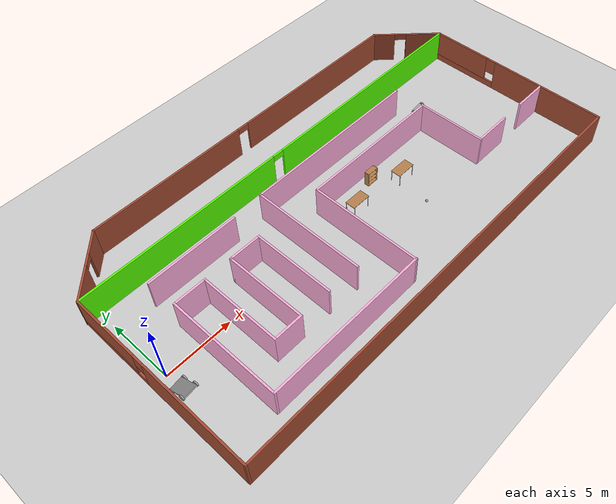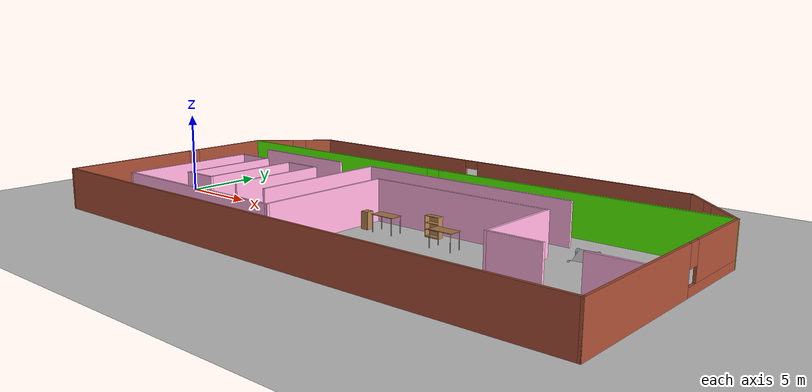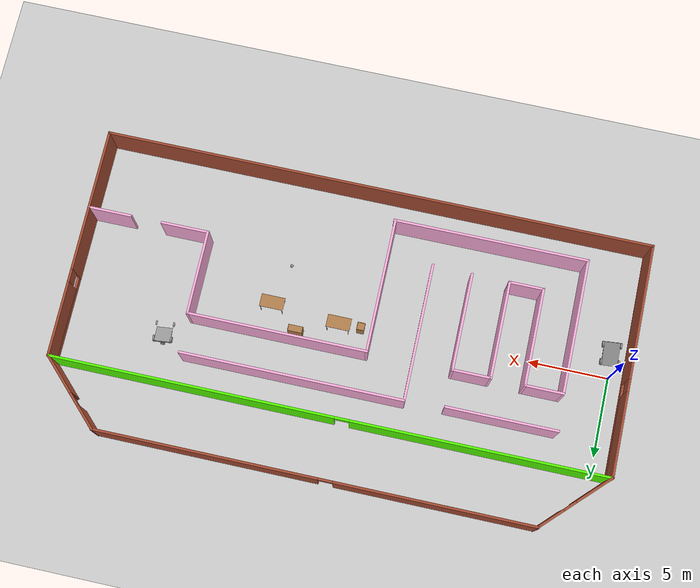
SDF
<sdf version="1.6">
 <world name="default">
  <plugin name="hello" filename="libhello.so"/>
  <light name="sun" type="directional">
   <pose>0 0 10 0 -0 0</pose>
   <diffuse>0.8 0.8 0.8 1</diffuse>
   <specular>0.2 0.2 0.2 1</specular>
   <attenuation>
    <range>1000</range>
    <constant>0.9</constant>
    <linear>0.01</linear>
    <quadratic>0.001</quadratic>
   </attenuation>
   <direction>-0.5 0.1 -0.9</direction>
  </light>
  <model name="ground_plane">
   <static>1</static>
   <link name="link">
    <collision name="collision">
     <geometry><plane><normal>0 0 1</normal><size>100 100</size></plane></geometry>
     <surface><friction><ode><mu>100</mu><mu2>50</mu2></ode></friction></surface>
    </collision>
    <visual name="visual">
     <cast_shadows>0</cast_shadows>
     <geometry><plane><normal>0 0 1</normal><size>100 100</size></plane></geometry>
     <material>
      <script><uri>file://media/materials/scripts/gazebo.material</uri><name>Gazebo/Grey</name></script>
     </material>
    </visual>
   </link>
  </model>
  <gravity>0 0 -9.8</gravity>
  <magnetic_field>6e-06 2.3e-05 -4.2e-05</magnetic_field>
  <atmosphere type="adiabatic"/>
  <physics name="default_physics" default="0" type="ode">
   <max_step_size>0.001</max_step_size>
   <real_time_factor>1</real_time_factor>
   <real_time_update_rate>1000</real_time_update_rate>
  </physics>
  <scene><ambient>0.4 0.4 0.4 1</ambient><background>0.7 0.7 0.7 1</background><shadows>1</shadows></scene>
  <spherical_coordinates>
   <surface_model>EARTH_WGS84</surface_model>
   <latitude_deg>0</latitude_deg>
   <longitude_deg>0</longitude_deg>
   <elevation>0</elevation>
   <heading_deg>0</heading_deg>
  </spherical_coordinates>
  <model name="MyRover">
   <link name="link_0">
    <pose>0.552858 -0.344643 -0.228571 3.14159 1.57079 3.14159</pose>
    <inertial>
     <mass>1</mass>
     <inertia><ixx>0.145833</ixx><ixy>0</ixy><ixz>0</ixz><iyy>0.145833</iyy><iyz>0</iyz><izz>0.125</izz></inertia>
    </inertial>
    <visual name="visual">
     <geometry><cylinder><radius>0.2</radius><length>0.1</length></cylinder></geometry>
     <material>
      <lighting>1</lighting>
      <script><uri>file://media/materials/scripts/gazebo.material</uri><name>Gazebo/Grey</name></script>
      <ambient>0.3 0.3 0.3 1</ambient>
      <diffuse>0.7 0.7 0.7 1</diffuse>
      <specular>0.01 0.01 0.01 1</specular>
      <emissive>0 0 0 1</emissive>
      <shader type="vertex"><normal_map>__default__</normal_map></shader>
     </material>
    </visual>
    <collision name="collision">
     <geometry><cylinder><radius>0.2</radius><length>0.1</length></cylinder></geometry>
     <surface>
      <friction>
       <ode><mu>1</mu><mu2>1</mu2><fdir1>0 0 0</fdir1><slip1>0</slip1><slip2>0</slip2></ode>
       <torsional>
        <coefficient>1</coefficient>
        <patch_radius>0</patch_radius>
        <surface_radius>0</surface_radius>
        <use_patch_radius>1</use_patch_radius>
        <ode><slip>0</slip></ode>
       </torsional>
      </friction>
      <bounce><restitution_coefficient>0</restitution_coefficient><threshold>1e+06</threshold></bounce>
      <contact>
       <collide_without_contact>0</collide_without_contact>
       <collide_without_contact_bitmask>1</collide_without_contact_bitmask>
       <collide_bitmask>1</collide_bitmask>
       <ode>
        <soft_cfm>0</soft_cfm>
        <soft_erp>0.2</soft_erp>
        <kp>1e+13</kp>
        <kd>1</kd>
        <max_vel>0.01</max_vel>
        <min_depth>0</min_depth>
       </ode>
       <bullet>
        <split_impulse>1</split_impulse>
        <split_impulse_penetration_threshold>-0.01</split_impulse_penetration_threshold>
        <soft_cfm>0</soft_cfm>
        <soft_erp>0.2</soft_erp>
        <kp>1e+13</kp>
        <kd>1</kd>
       </bullet>
      </contact>
     </surface>
    </collision>
   </link>
   <link name="link_0_clone">
    <pose>-0.547144 0.755357 -0.228571 3.14159 1.57079 3.14159</pose>
    <inertial>
     <mass>1</mass>
     <inertia><ixx>0.145833</ixx><ixy>0</ixy><ixz>0</ixz><iyy>0.145833</iyy><iyz>0</iyz><izz>0.125</izz></inertia>
    </inertial>
    <visual name="visual">
     <geometry><cylinder><radius>0.2</radius><length>0.1</length></cylinder></geometry>
     <material>
      <lighting>1</lighting>
      <script><uri>file://media/materials/scripts/gazebo.material</uri><name>Gazebo/Grey</name></script>
      <ambient>0.3 0.3 0.3 1</ambient>
      <diffuse>0.7 0.7 0.7 1</diffuse>
      <specular>0.01 0.01 0.01 1</specular>
      <emissive>0 0 0 1</emissive>
      <shader type="vertex"><normal_map>__default__</normal_map></shader>
     </material>
    </visual>
    <collision name="collision">
     <geometry><cylinder><radius>0.2</radius><length>0.1</length></cylinder></geometry>
     <surface>
      <friction>
       <ode><mu>1</mu><mu2>1</mu2><fdir1>0 0 0</fdir1><slip1>0</slip1><slip2>0</slip2></ode>
       <torsional>
        <coefficient>1</coefficient>
        <patch_radius>0</patch_radius>
        <surface_radius>0</surface_radius>
        <use_patch_radius>1</use_patch_radius>
        <ode><slip>0</slip></ode>
       </torsional>
      </friction>
      <bounce><restitution_coefficient>0</restitution_coefficient><threshold>1e+06</threshold></bounce>
      <contact>
       <collide_without_contact>0</collide_without_contact>
       <collide_without_contact_bitmask>1</collide_without_contact_bitmask>
       <collide_bitmask>1</collide_bitmask>
       <ode>
        <soft_cfm>0</soft_cfm>
        <soft_erp>0.2</soft_erp>
        <kp>1e+13</kp>
        <kd>1</kd>
        <max_vel>0.01</max_vel>
        <min_depth>0</min_depth>
       </ode>
       <bullet>
        <split_impulse>1</split_impulse>
        <split_impulse_penetration_threshold>-0.01</split_impulse_penetration_threshold>
        <soft_cfm>0</soft_cfm>
        <soft_erp>0.2</soft_erp>
        <kp>1e+13</kp>
        <kd>1</kd>
       </bullet>
      </contact>
     </surface>
    </collision>
   </link>
   <link name="link_0_clone_0">
    <pose>0.552858 0.755357 -0.228571 3.14159 1.57079 3.14159</pose>
    <inertial>
     <mass>1</mass>
     <inertia><ixx>0.145833</ixx><ixy>0</ixy><ixz>0</ixz><iyy>0.145833</iyy><iyz>0</iyz><izz>0.125</izz></inertia>
    </inertial>
    <visual name="visual">
     <geometry><cylinder><radius>0.2</radius><length>0.1</length></cylinder></geometry>
     <material>
      <lighting>1</lighting>
      <script><uri>file://media/materials/scripts/gazebo.material</uri><name>Gazebo/Grey</name></script>
      <ambient>0.3 0.3 0.3 1</ambient>
      <diffuse>0.7 0.7 0.7 1</diffuse>
      <specular>0.01 0.01 0.01 1</specular>
      <emissive>0 0 0 1</emissive>
      <shader type="vertex"><normal_map>__default__</normal_map></shader>
     </material>
    </visual>
    <collision name="collision">
     <geometry><cylinder><radius>0.2</radius><length>0.1</length></cylinder></geometry>
     <surface>
      <friction>
       <ode><mu>1</mu><mu2>1</mu2><fdir1>0 0 0</fdir1><slip1>0</slip1><slip2>0</slip2></ode>
       <torsional>
        <coefficient>1</coefficient>
        <patch_radius>0</patch_radius>
        <surface_radius>0</surface_radius>
        <use_patch_radius>1</use_patch_radius>
        <ode><slip>0</slip></ode>
       </torsional>
      </friction>
      <bounce><restitution_coefficient>0</restitution_coefficient><threshold>1e+06</threshold></bounce>
      <contact>
       <collide_without_contact>0</collide_without_contact>
       <collide_without_contact_bitmask>1</collide_without_contact_bitmask>
       <collide_bitmask>1</collide_bitmask>
       <ode>
        <soft_cfm>0</soft_cfm>
        <soft_erp>0.2</soft_erp>
        <kp>1e+13</kp>
        <kd>1</kd>
        <max_vel>0.01</max_vel>
        <min_depth>0</min_depth>
       </ode>
       <bullet>
        <split_impulse>1</split_impulse>
        <split_impulse_penetration_threshold>-0.01</split_impulse_penetration_threshold>
        <soft_cfm>0</soft_cfm>
        <soft_erp>0.2</soft_erp>
        <kp>1e+13</kp>
        <kd>1</kd>
       </bullet>
      </contact>
     </surface>
    </collision>
   </link>
   <link name="link_0_clone_1">
    <pose>-0.547144 -0.344643 -0.228571 3.14159 1.57079 3.14159</pose>
    <inertial>
     <mass>1</mass>
     <inertia><ixx>0.145833</ixx><ixy>0</ixy><ixz>0</ixz><iyy>0.145833</iyy><iyz>0</iyz><izz>0.125</izz></inertia>
    </inertial>
    <visual name="visual">
     <geometry><cylinder><radius>0.2</radius><length>0.1</length></cylinder></geometry>
     <material>
      <lighting>1</lighting>
      <script><uri>file://media/materials/scripts/gazebo.material</uri><name>Gazebo/Grey</name></script>
      <ambient>0.3 0.3 0.3 1</ambient>
      <diffuse>0.7 0.7 0.7 1</diffuse>
      <specular>0.01 0.01 0.01 1</specular>
      <emissive>0 0 0 1</emissive>
      <shader type="vertex"><normal_map>__default__</normal_map></shader>
     </material>
    </visual>
    <collision name="collision">
     <geometry><cylinder><radius>0.2</radius><length>0.1</length></cylinder></geometry>
     <surface>
      <friction>
       <ode><mu>1</mu><mu2>1</mu2><fdir1>0 0 0</fdir1><slip1>0</slip1><slip2>0</slip2></ode>
       <torsional>
        <coefficient>1</coefficient>
        <patch_radius>0</patch_radius>
        <surface_radius>0</surface_radius>
        <use_patch_radius>1</use_patch_radius>
        <ode><slip>0</slip></ode>
       </torsional>
      </friction>
      <bounce><restitution_coefficient>0</restitution_coefficient><threshold>1e+06</threshold></bounce>
      <contact>
       <collide_without_contact>0</collide_without_contact>
       <collide_without_contact_bitmask>1</collide_without_contact_bitmask>
       <collide_bitmask>1</collide_bitmask>
       <ode>
        <soft_cfm>0</soft_cfm>
        <soft_erp>0.2</soft_erp>
        <kp>1e+13</kp>
        <kd>1</kd>
        <max_vel>0.01</max_vel>
        <min_depth>0</min_depth>
       </ode>
       <bullet>
        <split_impulse>1</split_impulse>
        <split_impulse_penetration_threshold>-0.01</split_impulse_penetration_threshold>
        <soft_cfm>0</soft_cfm>
        <soft_erp>0.2</soft_erp>
        <kp>1e+13</kp>
        <kd>1</kd>
       </bullet>
      </contact>
     </surface>
    </collision>
   </link>
   <link name="link_1">
    <pose>0.002857 0.205357 -0.228571 0 -0 0</pose>
    <inertial>
     <mass>1</mass>
     <inertia>
      <ixx>0.166667</ixx>
      <ixy>0</ixy>
      <ixz>0</ixz>
      <iyy>0.166667</iyy>
      <iyz>0</iyz>
      <izz>0.166667</izz>
     </inertia>
    </inertial>
    <visual name="visual">
     <geometry><box><size>1 1.5 0.1</size></box></geometry>
     <material>
      <lighting>1</lighting>
      <script><uri>file://media/materials/scripts/gazebo.material</uri><name>Gazebo/Grey</name></script>
      <ambient>0.3 0.3 0.3 1</ambient>
      <diffuse>0.7 0.7 0.7 1</diffuse>
      <specular>0.01 0.01 0.01 1</specular>
      <emissive>0 0 0 1</emissive>
      <shader type="vertex"><normal_map>__default__</normal_map></shader>
     </material>
    </visual>
    <collision name="collision">
     <geometry><box><size>1 1.5 0.1</size></box></geometry>
     <surface>
      <friction>
       <ode><mu>1</mu><mu2>1</mu2><fdir1>0 0 0</fdir1><slip1>0</slip1><slip2>0</slip2></ode>
       <torsional>
        <coefficient>1</coefficient>
        <patch_radius>0</patch_radius>
        <surface_radius>0</surface_radius>
        <use_patch_radius>1</use_patch_radius>
        <ode><slip>0</slip></ode>
       </torsional>
      </friction>
      <bounce><restitution_coefficient>0</restitution_coefficient><threshold>1e+06</threshold></bounce>
      <contact>
       <collide_without_contact>0</collide_without_contact>
       <collide_without_contact_bitmask>1</collide_without_contact_bitmask>
       <collide_bitmask>1</collide_bitmask>
       <ode>
        <soft_cfm>0</soft_cfm>
        <soft_erp>0.2</soft_erp>
        <kp>1e+13</kp>
        <kd>1</kd>
        <max_vel>0.01</max_vel>
        <min_depth>0</min_depth>
       </ode>
       <bullet>
        <split_impulse>1</split_impulse>
        <split_impulse_penetration_threshold>-0.01</split_impulse_penetration_threshold>
        <soft_cfm>0</soft_cfm>
        <soft_erp>0.2</soft_erp>
        <kp>1e+13</kp>
        <kd>1</kd>
       </bullet>
      </contact>
     </surface>
    </collision>
   </link>
   <link name="link_2">
    <pose>-0.017143 -0.519643 0.321429 0 -0 0</pose>
    <inertial>
     <mass>1</mass>
     <inertia>
      <ixx>0.166667</ixx>
      <ixy>0</ixy>
      <ixz>0</ixz>
      <iyy>0.166667</iyy>
      <iyz>0</iyz>
      <izz>0.166667</izz>
     </inertia>
    </inertial>
    <visual name="visual">
     <geometry><box><size>0.25 0.05 1</size></box></geometry>
     <material>
      <lighting>1</lighting>
      <script><uri>file://media/materials/scripts/gazebo.material</uri><name>Gazebo/Grey</name></script>
      <ambient>0.3 0.3 0.3 1</ambient>
      <diffuse>0.7 0.7 0.7 1</diffuse>
      <specular>0.01 0.01 0.01 1</specular>
      <emissive>0 0 0 1</emissive>
      <shader type="vertex"><normal_map>__default__</normal_map></shader>
     </material>
    </visual>
    <collision name="collision">
     <geometry><box><size>0.25 0.05 1</size></box></geometry>
     <surface>
      <friction>
       <ode><mu>1</mu><mu2>1</mu2><fdir1>0 0 0</fdir1><slip1>0</slip1><slip2>0</slip2></ode>
       <torsional>
        <coefficient>1</coefficient>
        <patch_radius>0</patch_radius>
        <surface_radius>0</surface_radius>
        <use_patch_radius>1</use_patch_radius>
        <ode><slip>0</slip></ode>
       </torsional>
      </friction>
      <bounce><restitution_coefficient>0</restitution_coefficient><threshold>1e+06</threshold></bounce>
      <contact>
       <collide_without_contact>0</collide_without_contact>
       <collide_without_contact_bitmask>1</collide_without_contact_bitmask>
       <collide_bitmask>1</collide_bitmask>
       <ode>
        <soft_cfm>0</soft_cfm>
        <soft_erp>0.2</soft_erp>
        <kp>1e+13</kp>
        <kd>1</kd>
        <max_vel>0.01</max_vel>
        <min_depth>0</min_depth>
       </ode>
       <bullet>
        <split_impulse>1</split_impulse>
        <split_impulse_penetration_threshold>-0.01</split_impulse_penetration_threshold>
        <soft_cfm>0</soft_cfm>
        <soft_erp>0.2</soft_erp>
        <kp>1e+13</kp>
        <kd>1</kd>
       </bullet>
      </contact>
     </surface>
    </collision>
   </link>
   <link name="link_3">
    <pose>0.002857 -0.507143 0.821429 3.14159 1.57079 3.14159</pose>
    <inertial>
     <mass>1</mass>
     <inertia><ixx>0.145833</ixx><ixy>0</ixy><ixz>0</ixz><iyy>0.145833</iyy><iyz>0</iyz><izz>0.125</izz></inertia>
    </inertial>
    <visual name="visual">
     <geometry><cylinder><radius>0.05</radius><length>0.5</length></cylinder></geometry>
     <material>
      <lighting>1</lighting>
      <script><uri>file://media/materials/scripts/gazebo.material</uri><name>Gazebo/Grey</name></script>
      <ambient>0.3 0.3 0.3 1</ambient>
      <diffuse>0.7 0.7 0.7 1</diffuse>
      <specular>0.01 0.01 0.01 1</specular>
      <emissive>0 0 0 1</emissive>
      <shader type="vertex"><normal_map>__default__</normal_map></shader>
     </material>
    </visual>
    <collision name="collision">
     <geometry><cylinder><radius>0.05</radius><length>0.5</length></cylinder></geometry>
     <surface>
      <friction>
       <ode><mu>1</mu><mu2>1</mu2><fdir1>0 0 0</fdir1><slip1>0</slip1><slip2>0</slip2></ode>
       <torsional>
        <coefficient>1</coefficient>
        <patch_radius>0</patch_radius>
        <surface_radius>0</surface_radius>
        <use_patch_radius>1</use_patch_radius>
        <ode><slip>0</slip></ode>
       </torsional>
      </friction>
      <bounce><restitution_coefficient>0</restitution_coefficient><threshold>1e+06</threshold></bounce>
      <contact>
       <collide_without_contact>0</collide_without_contact>
       <collide_without_contact_bitmask>1</collide_without_contact_bitmask>
       <collide_bitmask>1</collide_bitmask>
       <ode>
        <soft_cfm>0</soft_cfm>
        <soft_erp>0.2</soft_erp>
        <kp>1e+13</kp>
        <kd>1</kd>
        <max_vel>0.01</max_vel>
        <min_depth>0</min_depth>
       </ode>
       <bullet>
        <split_impulse>1</split_impulse>
        <split_impulse_penetration_threshold>-0.01</split_impulse_penetration_threshold>
        <soft_cfm>0</soft_cfm>
        <soft_erp>0.2</soft_erp>
        <kp>1e+13</kp>
        <kd>1</kd>
       </bullet>
      </contact>
     </surface>
    </collision>
   </link>
   <joint name="link_1_JOINT_1" type="revolute">
    <parent>link_1</parent>
    <child>link_0</child>
    <axis>
     <xyz>0 0 1</xyz>
     <use_parent_model_frame>0</use_parent_model_frame>
     <limit>
      <lower>-1.79769e+308</lower>
      <upper>1.79769e+308</upper>
      <effort>-1</effort>
      <velocity>-1</velocity>
     </limit>
     <dynamics>
      <spring_reference>0</spring_reference>
      <spring_stiffness>0</spring_stiffness>
      <damping>0</damping>
     </dynamics>
    </axis>
    <physics>
     <ode><limit><cfm>0</cfm><erp>0.2</erp></limit><suspension><cfm>0</cfm><erp>0.2</erp></suspension></ode>
    </physics>
   </joint>
   <joint name="link_1_JOINT_2" type="revolute">
    <parent>link_1</parent>
    <child>link_0_clone_0</child>
    <pose>0 0 0 -0.02 0 0</pose>
    <axis>
     <xyz>0 0 1</xyz>
     <use_parent_model_frame>0</use_parent_model_frame>
     <limit>
      <lower>-1.79769e+308</lower>
      <upper>1.79769e+308</upper>
      <effort>-1</effort>
      <velocity>-1</velocity>
     </limit>
     <dynamics>
      <spring_reference>0</spring_reference>
      <spring_stiffness>0</spring_stiffness>
      <damping>0</damping>
     </dynamics>
    </axis>
    <physics>
     <ode><limit><cfm>0</cfm><erp>0.2</erp></limit><suspension><cfm>0</cfm><erp>0.2</erp></suspension></ode>
    </physics>
   </joint>
   <joint name="link_1_JOINT_4" type="revolute">
    <parent>link_1</parent>
    <child>link_0_clone</child>
    <axis>
     <xyz>0 0 1</xyz>
     <use_parent_model_frame>0</use_parent_model_frame>
     <limit>
      <lower>-1.79769e+308</lower>
      <upper>1.79769e+308</upper>
      <effort>-1</effort>
      <velocity>-1</velocity>
     </limit>
     <dynamics>
      <spring_reference>0</spring_reference>
      <spring_stiffness>0</spring_stiffness>
      <damping>0</damping>
     </dynamics>
    </axis>
    <physics>
     <ode><limit><cfm>0</cfm><erp>0.2</erp></limit><suspension><cfm>0</cfm><erp>0.2</erp></suspension></ode>
    </physics>
   </joint>
   <joint name="link_1_JOINT_5" type="revolute">
    <parent>link_1</parent>
    <child>link_0_clone_1</child>
    <axis>
     <xyz>0 0 1</xyz>
     <use_parent_model_frame>0</use_parent_model_frame>
     <limit>
      <lower>-1.79769e+308</lower>
      <upper>1.79769e+308</upper>
      <effort>-1</effort>
      <velocity>-1</velocity>
     </limit>
     <dynamics>
      <spring_reference>0</spring_reference>
      <spring_stiffness>0</spring_stiffness>
      <damping>0</damping>
     </dynamics>
    </axis>
    <physics>
     <ode><limit><cfm>0</cfm><erp>0.2</erp></limit><suspension><cfm>0</cfm><erp>0.2</erp></suspension></ode>
    </physics>
   </joint>
   <joint name="link_1_JOINT_6" type="fixed">
    <parent>link_1</parent>
    <child>link_2</child>
    <physics>
     <ode><limit><cfm>0</cfm><erp>0.2</erp></limit><suspension><cfm>0</cfm><erp>0.2</erp></suspension></ode>
    </physics>
   </joint>
   <joint name="link_2_JOINT_7" type="revolute">
    <parent>link_2</parent>
    <child>link_3</child>
    <axis>
     <xyz>0 0 1</xyz>
     <use_parent_model_frame>0</use_parent_model_frame>
     <limit>
      <lower>-1.79769e+308</lower>
      <upper>1.79769e+308</upper>
      <effort>-1</effort>
      <velocity>-1</velocity>
     </limit>
     <dynamics>
      <spring_reference>0</spring_reference>
      <spring_stiffness>0</spring_stiffness>
      <damping>0</damping>
     </dynamics>
    </axis>
    <physics>
     <ode><limit><cfm>0</cfm><erp>0.2</erp></limit><suspension><cfm>0</cfm><erp>0.2</erp></suspension></ode>
    </physics>
   </joint>
   <static>0</static>
   <pose>0.114675 -1.40874 0.12852 2.72972 1.2e-05 0.09666</pose>
  </model>
  <model name="Mybuilding">
   <pose>16.3545 0.96486 0 0 -0 0</pose>
   <link name="Wall_1">
    <collision name="Wall_1_Collision">
     <geometry><box><size>34.75 0.15 2.5</size></box></geometry>
     <pose>0 0 1.25 0 -0 0</pose>
    </collision>
    <visual name="Wall_1_Visual">
     <pose>0 0 1.25 0 -0 0</pose>
     <geometry><box><size>34.75 0.15 2.5</size></box></geometry>
     <material>
      <script><uri>file://media/materials/scripts/gazebo.material</uri><name>Gazebo/Bricks</name></script>
      <ambient>0.388235 0.368627 1 1</ambient>
     </material>
     <meta><layer>0</layer></meta>
    </visual>
    <pose>2e-06 -9.20704 0 0 -0 0</pose>
   </link>
   <link name="Wall_17">
    <collision name="Wall_17_Collision">
     <geometry><box><size>7 0.15 2.5</size></box></geometry>
     <pose>0 0 1.25 0 -0 0</pose>
    </collision>
    <visual name="Wall_17_Visual">
     <pose>0 0 1.25 0 -0 0</pose>
     <geometry><box><size>7 0.15 2.5</size></box></geometry>
     <material>
      <script><uri>file://media/materials/scripts/gazebo.material</uri><name>Gazebo/Grey</name></script>
      <ambient>1 0.686275 0.866667 1</ambient>
     </material>
     <meta><layer>0</layer></meta>
    </visual>
    <pose>-10.2308 3.33717 0 0 -0 0</pose>
   </link>
   <link name="Wall_2">
    <pose>17.3 -1.90704 0 0 -0 1.5708</pose>
    <visual name="Wall_2_Visual_0">
     <pose>-2.79021 0 1.25 0 -0 0</pose>
     <geometry><box><size>9.16958 0.15 2.5</size></box></geometry>
     <material>
      <script><uri>file://media/materials/scripts/gazebo.material</uri><name>Gazebo/Bricks</name></script>
      <ambient>0.388235 0.368627 1 1</ambient>
     </material>
     <meta><layer>0</layer></meta>
    </visual>
    <collision name="Wall_2_Collision_0">
     <geometry><box><size>9.16958 0.15 2.5</size></box></geometry>
     <pose>-2.79021 0 1.25 0 -0 0</pose>
    </collision>
    <visual name="Wall_2_Visual_1">
     <pose>4.58479 0 0.25 0 -0 0</pose>
     <geometry><box><size>5.58042 0.15 0.5</size></box></geometry>
     <material>
      <script><uri>file://media/materials/scripts/gazebo.material</uri><name>Gazebo/Bricks</name></script>
      <ambient>0.388235 0.368627 1 1</ambient>
     </material>
     <meta><layer>0</layer></meta>
    </visual>
    <collision name="Wall_2_Collision_1">
     <geometry><box><size>5.58042 0.15 0.5</size></box></geometry>
     <pose>4.58479 0 0.25 0 -0 0</pose>
    </collision>
    <visual name="Wall_2_Visual_2">
     <pose>4.98479 0 1.5 0 -0 0</pose>
     <geometry><box><size>4.78042 0.15 2</size></box></geometry>
     <material>
      <script><uri>file://media/materials/scripts/gazebo.material</uri><name>Gazebo/Bricks</name></script>
      <ambient>0.388235 0.368627 1 1</ambient>
     </material>
     <meta><layer>0</layer></meta>
    </visual>
    <collision name="Wall_2_Collision_2">
     <geometry><box><size>4.78042 0.15 2</size></box></geometry>
     <pose>4.98479 0 1.5 0 -0 0</pose>
    </collision>
    <visual name="Wall_2_Visual_3">
     <pose>2.19458 0 1.9 0 -0 0</pose>
     <geometry><box><size>0.8 0.15 1.2</size></box></geometry>
     <material>
      <script><uri>file://media/materials/scripts/gazebo.material</uri><name>Gazebo/Bricks</name></script>
      <ambient>0.388235 0.368627 1 1</ambient>
     </material>
     <meta><layer>0</layer></meta>
    </visual>
    <collision name="Wall_2_Collision_3">
     <geometry><box><size>0.8 0.15 1.2</size></box></geometry>
     <pose>2.19458 0 1.9 0 -0 0</pose>
    </collision>
   </link>
   <link name="Wall_22">
    <collision name="Wall_22_Collision">
     <geometry><box><size>14 0.15 2.5</size></box></geometry>
     <pose>0 0 1.25 0 -0 0</pose>
    </collision>
    <visual name="Wall_22_Visual">
     <pose>0 0 1.25 0 -0 0</pose>
     <geometry><box><size>14 0.15 2.5</size></box></geometry>
     <material>
      <script><uri>file://media/materials/scripts/gazebo.material</uri><name>Gazebo/Grey</name></script>
      <ambient>1 0.686275 0.866667 1</ambient>
     </material>
     <meta><layer>0</layer></meta>
    </visual>
    <pose>2.66567 3.49768 0 0 -0 0</pose>
   </link>
   <link name="Wall_3">
    <pose>2e-06 5.39296 0 0 -0 3.14159</pose>
    <visual name="Wall_3_Visual_0">
     <pose>-8.47813 0 1.25 0 -0 0</pose>
     <geometry><box><size>17.7937 0.15 2.5</size></box></geometry>
     <material>
      <script><uri>file://media/materials/scripts/gazebo.material</uri><name>Gazebo/Grey</name></script>
      <ambient>0.333333 1 0 1</ambient>
     </material>
     <meta><layer>0</layer></meta>
    </visual>
    <collision name="Wall_3_Collision_0">
     <geometry><box><size>17.7937 0.15 2.5</size></box></geometry>
     <pose>-8.47813 0 1.25 0 -0 0</pose>
    </collision>
    <visual name="Wall_3_Visual_1">
     <pose>9.34686 0 1.25 0 -0 0</pose>
     <geometry><box><size>16.0563 0.15 2.5</size></box></geometry>
     <material>
      <script><uri>file://media/materials/scripts/gazebo.material</uri><name>Gazebo/Grey</name></script>
      <ambient>0.333333 1 0 1</ambient>
     </material>
     <meta><layer>0</layer></meta>
    </visual>
    <collision name="Wall_3_Collision_1">
     <geometry><box><size>16.0563 0.15 2.5</size></box></geometry>
     <pose>9.34686 0 1.25 0 -0 0</pose>
    </collision>
    <visual name="Wall_3_Visual_2">
     <pose>0.86873 0 2.25 0 -0 0</pose>
     <geometry><box><size>0.9 0.15 0.5</size></box></geometry>
     <material>
      <script><uri>file://media/materials/scripts/gazebo.material</uri><name>Gazebo/Grey</name></script>
      <ambient>0.333333 1 0 1</ambient>
     </material>
     <meta><layer>0</layer></meta>
    </visual>
    <collision name="Wall_3_Collision_2">
     <geometry><box><size>0.9 0.15 0.5</size></box></geometry>
     <pose>0.86873 0 2.25 0 -0 0</pose>
    </collision>
   </link>
   <link name="Wall_30">
    <collision name="Wall_30_Collision">
     <geometry><box><size>12.25 0.15 2.5</size></box></geometry>
     <pose>0 0 1.25 0 -0 0</pose>
    </collision>
    <visual name="Wall_30_Visual">
     <pose>0 0 1.25 0 -0 0</pose>
     <geometry><box><size>12.25 0.15 2.5</size></box></geometry>
     <material>
      <script><uri>file://media/materials/scripts/gazebo.material</uri><name>Gazebo/Grey</name></script>
      <ambient>1 0.686275 0.866667 1</ambient>
     </material>
     <meta><layer>0</layer></meta>
    </visual>
    <pose>-7.45232 -7.43831 0 0 -0 3.14159</pose>
   </link>
   <link name="Wall_31">
    <collision name="Wall_31_Collision">
     <geometry><box><size>8.62565 0.15 2.5</size></box></geometry>
     <pose>0 0 1.25 0 -0 0</pose>
    </collision>
    <visual name="Wall_31_Visual">
     <pose>0 0 1.25 0 -0 0</pose>
     <geometry><box><size>8.62565 0.15 2.5</size></box></geometry>
     <material>
      <script><uri>file://media/materials/scripts/gazebo.material</uri><name>Gazebo/Grey</name></script>
      <ambient>1 0.686275 0.866667 1</ambient>
     </material>
     <meta><layer>0</layer></meta>
    </visual>
    <pose>-13.5558 -3.20057 0 0 -0 1.5708</pose>
   </link>
   <link name="Wall_32">
    <collision name="Wall_32_Collision">
     <geometry><box><size>2.5 0.15 2.5</size></box></geometry>
     <pose>0 0 1.25 0 -0 0</pose>
    </collision>
    <visual name="Wall_32_Visual">
     <pose>0 0 1.25 0 -0 0</pose>
     <geometry><box><size>2.5 0.15 2.5</size></box></geometry>
     <material>
      <script><uri>file://media/materials/scripts/gazebo.material</uri><name>Gazebo/Grey</name></script>
      <ambient>1 0.686275 0.866667 1</ambient>
     </material>
     <meta><layer>0</layer></meta>
    </visual>
    <pose>-12.3808 1.03717 0 0 -0 0</pose>
   </link>
   <link name="Wall_33">
    <collision name="Wall_33_Collision">
     <geometry><box><size>6.25 0.15 2.5</size></box></geometry>
     <pose>0 0 1.25 0 -0 0</pose>
    </collision>
    <visual name="Wall_33_Visual">
     <pose>0 0 1.25 0 -0 0</pose>
     <geometry><box><size>6.25 0.15 2.5</size></box></geometry>
     <material>
      <script><uri>file://media/materials/scripts/gazebo.material</uri><name>Gazebo/Grey</name></script>
      <ambient>1 0.686275 0.866667 1</ambient>
     </material>
     <meta><layer>0</layer></meta>
    </visual>
    <pose>-11.2058 -2.01282 0 0 0 -1.5708</pose>
   </link>
   <link name="Wall_34">
    <collision name="Wall_34_Collision">
     <geometry><box><size>2.25 0.15 2.5</size></box></geometry>
     <pose>0 0 1.25 0 -0 0</pose>
    </collision>
    <visual name="Wall_34_Visual">
     <pose>0 0 1.25 0 -0 0</pose>
     <geometry><box><size>2.25 0.15 2.5</size></box></geometry>
     <material>
      <script><uri>file://media/materials/scripts/gazebo.material</uri><name>Gazebo/Grey</name></script>
      <ambient>1 0.686275 0.866667 1</ambient>
     </material>
     <meta><layer>0</layer></meta>
    </visual>
    <pose>-10.1558 -5.06283 0 0 -0 0</pose>
   </link>
   <link name="Wall_37">
    <collision name="Wall_37_Collision">
     <geometry><box><size>8.62565 0.15 2.5</size></box></geometry>
     <pose>0 0 1.25 0 -0 0</pose>
    </collision>
    <visual name="Wall_37_Visual">
     <pose>0 0 1.25 0 -0 0</pose>
     <geometry><box><size>8.62565 0.15 2.5</size></box></geometry>
     <material>
      <script><uri>file://media/materials/scripts/gazebo.material</uri><name>Gazebo/Grey</name></script>
      <ambient>1 0.686275 0.866667 1</ambient>
     </material>
     <meta><layer>0</layer></meta>
    </visual>
    <pose>-1.45582 -3.20057 0 0 -0 1.5708</pose>
   </link>
   <link name="Wall_38">
    <collision name="Wall_38_Collision">
     <geometry><box><size>11.3181 0.15 2.5</size></box></geometry>
     <pose>0 0 1.25 0 -0 0</pose>
    </collision>
    <visual name="Wall_38_Visual">
     <pose>0 0 1.25 0 -0 0</pose>
     <geometry><box><size>11.3181 0.15 2.5</size></box></geometry>
     <material>
      <script><uri>file://media/materials/scripts/gazebo.material</uri><name>Gazebo/Grey</name></script>
      <ambient>1 0.686275 0.866667 1</ambient>
     </material>
     <meta><layer>0</layer></meta>
    </visual>
    <pose>4.12824 1.03717 0 0 -0 0</pose>
   </link>
   <link name="Wall_45">
    <collision name="Wall_45_Collision">
     <geometry><box><size>6.25 0.15 2.5</size></box></geometry>
     <pose>0 0 1.25 0 -0 0</pose>
    </collision>
    <visual name="Wall_45_Visual">
     <pose>0 0 1.25 0 -0 0</pose>
     <geometry><box><size>6.25 0.15 2.5</size></box></geometry>
     <material>
      <script><uri>file://media/materials/scripts/gazebo.material</uri><name>Gazebo/Grey</name></script>
      <ambient>1 0.686275 0.866667 1</ambient>
     </material>
     <meta><layer>0</layer></meta>
    </visual>
    <pose>-9.10582 -2.01282 0 0 -0 1.5708</pose>
   </link>
   <link name="Wall_46">
    <collision name="Wall_46_Collision">
     <geometry><box><size>2.5 0.15 2.5</size></box></geometry>
     <pose>0 0 1.25 0 -0 0</pose>
    </collision>
    <visual name="Wall_46_Visual">
     <pose>0 0 1.25 0 -0 0</pose>
     <geometry><box><size>2.5 0.15 2.5</size></box></geometry>
     <material>
      <script><uri>file://media/materials/scripts/gazebo.material</uri><name>Gazebo/Grey</name></script>
      <ambient>1 0.686275 0.866667 1</ambient>
     </material>
     <meta><layer>0</layer></meta>
    </visual>
    <pose>-7.93083 1.03717 0 0 -0 0</pose>
   </link>
   <link name="Wall_5">
    <pose>-17.3 -1.90704 0 0 -0 1.5708</pose>
    <visual name="Wall_5_Visual_0">
     <pose>-3.08448 0 1.25 0 -0 0</pose>
     <geometry><box><size>8.58105 0.15 2.5</size></box></geometry>
     <material>
      <script><uri>file://media/materials/scripts/gazebo.material</uri><name>Gazebo/Bricks</name></script>
      <ambient>0.388235 0.368627 1 1</ambient>
     </material>
     <meta><layer>0</layer></meta>
    </visual>
    <collision name="Wall_5_Collision_0">
     <geometry><box><size>8.58105 0.15 2.5</size></box></geometry>
     <pose>-3.08448 0 1.25 0 -0 0</pose>
    </collision>
    <visual name="Wall_5_Visual_1">
     <pose>4.29052 0 0.25 0 -0 0</pose>
     <geometry><box><size>6.16895 0.15 0.5</size></box></geometry>
     <material>
      <script><uri>file://media/materials/scripts/gazebo.material</uri><name>Gazebo/Bricks</name></script>
      <ambient>0.388235 0.368627 1 1</ambient>
     </material>
     <meta><layer>0</layer></meta>
    </visual>
    <collision name="Wall_5_Collision_1">
     <geometry><box><size>6.16895 0.15 0.5</size></box></geometry>
     <pose>4.29052 0 0.25 0 -0 0</pose>
    </collision>
    <visual name="Wall_5_Visual_2">
     <pose>4.69052 0 1.5 0 -0 0</pose>
     <geometry><box><size>5.36895 0.15 2</size></box></geometry>
     <material>
      <script><uri>file://media/materials/scripts/gazebo.material</uri><name>Gazebo/Bricks</name></script>
      <ambient>0.388235 0.368627 1 1</ambient>
     </material>
     <meta><layer>0</layer></meta>
    </visual>
    <collision name="Wall_5_Collision_2">
     <geometry><box><size>5.36895 0.15 2</size></box></geometry>
     <pose>4.69052 0 1.5 0 -0 0</pose>
    </collision>
    <visual name="Wall_5_Visual_3">
     <pose>1.60605 0 1.9 0 -0 0</pose>
     <geometry><box><size>0.8 0.15 1.2</size></box></geometry>
     <material>
      <script><uri>file://media/materials/scripts/gazebo.material</uri><name>Gazebo/Bricks</name></script>
      <ambient>0.388235 0.368627 1 1</ambient>
     </material>
     <meta><layer>0</layer></meta>
    </visual>
    <collision name="Wall_5_Collision_3">
     <geometry><box><size>0.8 0.15 1.2</size></box></geometry>
     <pose>1.60605 0 1.9 0 -0 0</pose>
    </collision>
   </link>
   <link name="Wall_50">
    <collision name="Wall_50_Collision">
     <geometry><box><size>6.25 0.15 2.5</size></box></geometry>
     <pose>0 0 1.25 0 -0 0</pose>
    </collision>
    <visual name="Wall_50_Visual">
     <pose>0 0 1.25 0 -0 0</pose>
     <geometry><box><size>6.25 0.15 2.5</size></box></geometry>
     <material>
      <script><uri>file://media/materials/scripts/gazebo.material</uri><name>Gazebo/Grey</name></script>
      <ambient>1 0.686275 0.866667 1</ambient>
     </material>
     <meta><layer>0</layer></meta>
    </visual>
    <pose>-6.75583 -2.01282 0 0 0 -1.5708</pose>
   </link>
   <link name="Wall_52">
    <collision name="Wall_52_Collision">
     <geometry><box><size>8.75 0.15 2.5</size></box></geometry>
     <pose>0 0 1.25 0 -0 0</pose>
    </collision>
    <visual name="Wall_52_Visual">
     <pose>0 0 1.25 0 -0 0</pose>
     <geometry><box><size>8.75 0.15 2.5</size></box></geometry>
     <material>
      <script><uri>file://media/materials/scripts/gazebo.material</uri><name>Gazebo/Grey</name></script>
      <ambient>1 0.686275 0.866667 1</ambient>
     </material>
     <meta><layer>0</layer></meta>
    </visual>
    <pose>-4.29289 -0.816935 0 0 0 -1.5708</pose>
   </link>
   <link name="Wall_59">
    <collision name="Wall_59_Collision">
     <geometry><box><size>5.39327 0.15 2.5</size></box></geometry>
     <pose>0 0 1.25 0 -0 0</pose>
    </collision>
    <visual name="Wall_59_Visual">
     <pose>0 0 1.25 0 -0 0</pose>
     <geometry><box><size>5.39327 0.15 2.5</size></box></geometry>
     <material>
      <script><uri>file://media/materials/scripts/gazebo.material</uri><name>Gazebo/Grey</name></script>
      <ambient>1 0.686275 0.866667 1</ambient>
     </material>
     <meta><layer>0</layer></meta>
    </visual>
    <pose>9.71229 -1.58432 0 0 0 -1.5708</pose>
   </link>
   <link name="Wall_60">
    <collision name="Wall_60_Collision">
     <geometry><box><size>3 0.15 2.5</size></box></geometry>
     <pose>0 0 1.25 0 -0 0</pose>
    </collision>
    <visual name="Wall_60_Visual">
     <pose>0 0 1.25 0 -0 0</pose>
     <geometry><box><size>3 0.15 2.5</size></box></geometry>
     <material>
      <script><uri>file://media/materials/scripts/gazebo.material</uri><name>Gazebo/Grey</name></script>
      <ambient>1 0.686275 0.866667 1</ambient>
     </material>
     <meta><layer>0</layer></meta>
    </visual>
    <pose>11.1908 -4.20582 0 0 -0 0</pose>
   </link>
   <link name="Wall_62">
    <collision name="Wall_62_Collision">
     <geometry><box><size>2.75 0.15 2.5</size></box></geometry>
     <pose>0 0 1.25 0 -0 0</pose>
    </collision>
    <visual name="Wall_62_Visual">
     <pose>0 0 1.25 0 -0 0</pose>
     <geometry><box><size>2.75 0.15 2.5</size></box></geometry>
     <material>
      <script><uri>file://media/materials/scripts/gazebo.material</uri><name>Gazebo/Grey</name></script>
      <ambient>1 0.686275 0.866667 1</ambient>
     </material>
     <meta><layer>0</layer></meta>
    </visual>
    <pose>15.947 -4.20668 0 0 -0 0</pose>
   </link>
   <link name="Wall_7">
    <pose>-15.4085 7.28447 0 0 -0 0.785398</pose>
    <visual name="Wall_7_Visual_0">
     <pose>-1.4112 0 1.25 0 -0 0</pose>
     <geometry><box><size>2.67759 0.15 2.5</size></box></geometry>
     <material>
      <script><uri>file://media/materials/scripts/gazebo.material</uri><name>Gazebo/Bricks</name></script>
      <ambient>0.388235 0.368627 1 1</ambient>
     </material>
     <meta><layer>0</layer></meta>
    </visual>
    <collision name="Wall_7_Collision_0">
     <geometry><box><size>2.67759 0.15 2.5</size></box></geometry>
     <pose>-1.4112 0 1.25 0 -0 0</pose>
    </collision>
    <visual name="Wall_7_Visual_1">
     <pose>1.7888 0 1.25 0 -0 0</pose>
     <geometry><box><size>1.92241 0.15 2.5</size></box></geometry>
     <material>
      <script><uri>file://media/materials/scripts/gazebo.material</uri><name>Gazebo/Bricks</name></script>
      <ambient>0.388235 0.368627 1 1</ambient>
     </material>
     <meta><layer>0</layer></meta>
    </visual>
    <collision name="Wall_7_Collision_1">
     <geometry><box><size>1.92241 0.15 2.5</size></box></geometry>
     <pose>1.7888 0 1.25 0 -0 0</pose>
    </collision>
    <visual name="Wall_7_Visual_2">
     <pose>0.377593 0 2.25 0 -0 0</pose>
     <geometry><box><size>0.9 0.15 0.5</size></box></geometry>
     <material>
      <script><uri>file://media/materials/scripts/gazebo.material</uri><name>Gazebo/Bricks</name></script>
      <ambient>0.388235 0.368627 1 1</ambient>
     </material>
     <meta><layer>0</layer></meta>
    </visual>
    <collision name="Wall_7_Collision_2">
     <geometry><box><size>0.9 0.15 0.5</size></box></geometry>
     <pose>0.377593 0 2.25 0 -0 0</pose>
    </collision>
   </link>
   <link name="Wall_8">
    <pose>0.033023 9.17598 0 0 -0 0</pose>
    <visual name="Wall_8_Visual_0">
     <pose>-7.40812 0 1.25 0 -0 0</pose>
     <geometry><box><size>12.4338 0.15 2.5</size></box></geometry>
     <material>
      <script><uri>file://media/materials/scripts/gazebo.material</uri><name>Gazebo/Bricks</name></script>
      <ambient>0.388235 0.368627 1 1</ambient>
     </material>
     <meta><layer>0</layer></meta>
    </visual>
    <collision name="Wall_8_Collision_0">
     <geometry><box><size>12.4338 0.15 2.5</size></box></geometry>
     <pose>-7.40812 0 1.25 0 -0 0</pose>
    </collision>
    <visual name="Wall_8_Visual_1">
     <pose>6.66688 0 1.25 0 -0 0</pose>
     <geometry><box><size>13.9162 0.15 2.5</size></box></geometry>
     <material>
      <script><uri>file://media/materials/scripts/gazebo.material</uri><name>Gazebo/Bricks</name></script>
      <ambient>0.388235 0.368627 1 1</ambient>
     </material>
     <meta><layer>0</layer></meta>
    </visual>
    <collision name="Wall_8_Collision_1">
     <geometry><box><size>13.9162 0.15 2.5</size></box></geometry>
     <pose>6.66688 0 1.25 0 -0 0</pose>
    </collision>
    <visual name="Wall_8_Visual_2">
     <pose>-0.741243 0 2.25 0 -0 0</pose>
     <geometry><box><size>0.9 0.15 0.5</size></box></geometry>
     <material>
      <script><uri>file://media/materials/scripts/gazebo.material</uri><name>Gazebo/Bricks</name></script>
      <ambient>0.388235 0.368627 1 1</ambient>
     </material>
     <meta><layer>0</layer></meta>
    </visual>
    <collision name="Wall_8_Collision_2">
     <geometry><box><size>0.9 0.15 0.5</size></box></geometry>
     <pose>-0.741243 0 2.25 0 -0 0</pose>
    </collision>
   </link>
   <link name="Wall_9">
    <pose>15.4415 7.28447 0 0 0 -0.794204</pose>
    <visual name="Wall_9_Visual_0">
     <pose>-1.85429 0 1.25 0 -0 0</pose>
     <geometry><box><size>1.74493 0.15 2.5</size></box></geometry>
     <material>
      <script><uri>file://media/materials/scripts/gazebo.material</uri><name>Gazebo/Bricks</name></script>
      <ambient>0.388235 0.368627 1 1</ambient>
     </material>
     <meta><layer>0</layer></meta>
    </visual>
    <collision name="Wall_9_Collision_0">
     <geometry><box><size>1.74493 0.15 2.5</size></box></geometry>
     <pose>-1.85429 0 1.25 0 -0 0</pose>
    </collision>
    <visual name="Wall_9_Visual_1">
     <pose>1.32247 0 1.25 0 -0 0</pose>
     <geometry><box><size>2.80857 0.15 2.5</size></box></geometry>
     <material>
      <script><uri>file://media/materials/scripts/gazebo.material</uri><name>Gazebo/Bricks</name></script>
      <ambient>0.388235 0.368627 1 1</ambient>
     </material>
     <meta><layer>0</layer></meta>
    </visual>
    <collision name="Wall_9_Collision_1">
     <geometry><box><size>2.80857 0.15 2.5</size></box></geometry>
     <pose>1.32247 0 1.25 0 -0 0</pose>
    </collision>
    <visual name="Wall_9_Visual_2">
     <pose>-0.531822 0 2.25 0 -0 0</pose>
     <geometry><box><size>0.9 0.15 0.5</size></box></geometry>
     <material>
      <script><uri>file://media/materials/scripts/gazebo.material</uri><name>Gazebo/Bricks</name></script>
      <ambient>0.388235 0.368627 1 1</ambient>
     </material>
     <meta><layer>0</layer></meta>
    </visual>
    <collision name="Wall_9_Collision_2">
     <geometry><box><size>0.9 0.15 0.5</size></box></geometry>
     <pose>-0.531822 0 2.25 0 -0 0</pose>
    </collision>
   </link>
   <static>1</static>
  </model>
  <model name="MyRover_0">
   <link name="link_0">
    <pose>0.552858 -0.344643 -0.228571 3.14159 1.57079 3.14159</pose>
    <inertial>
     <mass>1</mass>
     <inertia><ixx>0.145833</ixx><ixy>0</ixy><ixz>0</ixz><iyy>0.145833</iyy><iyz>0</iyz><izz>0.125</izz></inertia>
    </inertial>
    <visual name="visual">
     <geometry><cylinder><radius>0.2</radius><length>0.1</length></cylinder></geometry>
     <material>
      <lighting>1</lighting>
      <script><uri>file://media/materials/scripts/gazebo.material</uri><name>Gazebo/Grey</name></script>
      <ambient>0.3 0.3 0.3 1</ambient>
      <diffuse>0.7 0.7 0.7 1</diffuse>
      <specular>0.01 0.01 0.01 1</specular>
      <emissive>0 0 0 1</emissive>
      <shader type="vertex"><normal_map>__default__</normal_map></shader>
     </material>
    </visual>
    <collision name="collision">
     <geometry><cylinder><radius>0.2</radius><length>0.1</length></cylinder></geometry>
     <surface>
      <friction>
       <ode><mu>1</mu><mu2>1</mu2><fdir1>0 0 0</fdir1><slip1>0</slip1><slip2>0</slip2></ode>
       <torsional>
        <coefficient>1</coefficient>
        <patch_radius>0</patch_radius>
        <surface_radius>0</surface_radius>
        <use_patch_radius>1</use_patch_radius>
        <ode><slip>0</slip></ode>
       </torsional>
      </friction>
      <bounce><restitution_coefficient>0</restitution_coefficient><threshold>1e+06</threshold></bounce>
      <contact>
       <collide_without_contact>0</collide_without_contact>
       <collide_without_contact_bitmask>1</collide_without_contact_bitmask>
       <collide_bitmask>1</collide_bitmask>
       <ode>
        <soft_cfm>0</soft_cfm>
        <soft_erp>0.2</soft_erp>
        <kp>1e+13</kp>
        <kd>1</kd>
        <max_vel>0.01</max_vel>
        <min_depth>0</min_depth>
       </ode>
       <bullet>
        <split_impulse>1</split_impulse>
        <split_impulse_penetration_threshold>-0.01</split_impulse_penetration_threshold>
        <soft_cfm>0</soft_cfm>
        <soft_erp>0.2</soft_erp>
        <kp>1e+13</kp>
        <kd>1</kd>
       </bullet>
      </contact>
     </surface>
    </collision>
   </link>
   <link name="link_0_clone">
    <pose>-0.547144 0.755357 -0.228571 3.14159 1.57079 3.14159</pose>
    <inertial>
     <mass>1</mass>
     <inertia><ixx>0.145833</ixx><ixy>0</ixy><ixz>0</ixz><iyy>0.145833</iyy><iyz>0</iyz><izz>0.125</izz></inertia>
    </inertial>
    <visual name="visual">
     <geometry><cylinder><radius>0.2</radius><length>0.1</length></cylinder></geometry>
     <material>
      <lighting>1</lighting>
      <script><uri>file://media/materials/scripts/gazebo.material</uri><name>Gazebo/Grey</name></script>
      <ambient>0.3 0.3 0.3 1</ambient>
      <diffuse>0.7 0.7 0.7 1</diffuse>
      <specular>0.01 0.01 0.01 1</specular>
      <emissive>0 0 0 1</emissive>
      <shader type="vertex"><normal_map>__default__</normal_map></shader>
     </material>
    </visual>
    <collision name="collision">
     <geometry><cylinder><radius>0.2</radius><length>0.1</length></cylinder></geometry>
     <surface>
      <friction>
       <ode><mu>1</mu><mu2>1</mu2><fdir1>0 0 0</fdir1><slip1>0</slip1><slip2>0</slip2></ode>
       <torsional>
        <coefficient>1</coefficient>
        <patch_radius>0</patch_radius>
        <surface_radius>0</surface_radius>
        <use_patch_radius>1</use_patch_radius>
        <ode><slip>0</slip></ode>
       </torsional>
      </friction>
      <bounce><restitution_coefficient>0</restitution_coefficient><threshold>1e+06</threshold></bounce>
      <contact>
       <collide_without_contact>0</collide_without_contact>
       <collide_without_contact_bitmask>1</collide_without_contact_bitmask>
       <collide_bitmask>1</collide_bitmask>
       <ode>
        <soft_cfm>0</soft_cfm>
        <soft_erp>0.2</soft_erp>
        <kp>1e+13</kp>
        <kd>1</kd>
        <max_vel>0.01</max_vel>
        <min_depth>0</min_depth>
       </ode>
       <bullet>
        <split_impulse>1</split_impulse>
        <split_impulse_penetration_threshold>-0.01</split_impulse_penetration_threshold>
        <soft_cfm>0</soft_cfm>
        <soft_erp>0.2</soft_erp>
        <kp>1e+13</kp>
        <kd>1</kd>
       </bullet>
      </contact>
     </surface>
    </collision>
   </link>
   <link name="link_0_clone_0">
    <pose>0.552858 0.755357 -0.228571 3.14159 1.57079 3.14159</pose>
    <inertial>
     <mass>1</mass>
     <inertia><ixx>0.145833</ixx><ixy>0</ixy><ixz>0</ixz><iyy>0.145833</iyy><iyz>0</iyz><izz>0.125</izz></inertia>
    </inertial>
    <visual name="visual">
     <geometry><cylinder><radius>0.2</radius><length>0.1</length></cylinder></geometry>
     <material>
      <lighting>1</lighting>
      <script><uri>file://media/materials/scripts/gazebo.material</uri><name>Gazebo/Grey</name></script>
      <ambient>0.3 0.3 0.3 1</ambient>
      <diffuse>0.7 0.7 0.7 1</diffuse>
      <specular>0.01 0.01 0.01 1</specular>
      <emissive>0 0 0 1</emissive>
      <shader type="vertex"><normal_map>__default__</normal_map></shader>
     </material>
    </visual>
    <collision name="collision">
     <geometry><cylinder><radius>0.2</radius><length>0.1</length></cylinder></geometry>
     <surface>
      <friction>
       <ode><mu>1</mu><mu2>1</mu2><fdir1>0 0 0</fdir1><slip1>0</slip1><slip2>0</slip2></ode>
       <torsional>
        <coefficient>1</coefficient>
        <patch_radius>0</patch_radius>
        <surface_radius>0</surface_radius>
        <use_patch_radius>1</use_patch_radius>
        <ode><slip>0</slip></ode>
       </torsional>
      </friction>
      <bounce><restitution_coefficient>0</restitution_coefficient><threshold>1e+06</threshold></bounce>
      <contact>
       <collide_without_contact>0</collide_without_contact>
       <collide_without_contact_bitmask>1</collide_without_contact_bitmask>
       <collide_bitmask>1</collide_bitmask>
       <ode>
        <soft_cfm>0</soft_cfm>
        <soft_erp>0.2</soft_erp>
        <kp>1e+13</kp>
        <kd>1</kd>
        <max_vel>0.01</max_vel>
        <min_depth>0</min_depth>
       </ode>
       <bullet>
        <split_impulse>1</split_impulse>
        <split_impulse_penetration_threshold>-0.01</split_impulse_penetration_threshold>
        <soft_cfm>0</soft_cfm>
        <soft_erp>0.2</soft_erp>
        <kp>1e+13</kp>
        <kd>1</kd>
       </bullet>
      </contact>
     </surface>
    </collision>
   </link>
   <link name="link_0_clone_1">
    <pose>-0.547144 -0.344643 -0.228571 3.14159 1.57079 3.14159</pose>
    <inertial>
     <mass>1</mass>
     <inertia><ixx>0.145833</ixx><ixy>0</ixy><ixz>0</ixz><iyy>0.145833</iyy><iyz>0</iyz><izz>0.125</izz></inertia>
    </inertial>
    <visual name="visual">
     <geometry><cylinder><radius>0.2</radius><length>0.1</length></cylinder></geometry>
     <material>
      <lighting>1</lighting>
      <script><uri>file://media/materials/scripts/gazebo.material</uri><name>Gazebo/Grey</name></script>
      <ambient>0.3 0.3 0.3 1</ambient>
      <diffuse>0.7 0.7 0.7 1</diffuse>
      <specular>0.01 0.01 0.01 1</specular>
      <emissive>0 0 0 1</emissive>
      <shader type="vertex"><normal_map>__default__</normal_map></shader>
     </material>
    </visual>
    <collision name="collision">
     <geometry><cylinder><radius>0.2</radius><length>0.1</length></cylinder></geometry>
     <surface>
      <friction>
       <ode><mu>1</mu><mu2>1</mu2><fdir1>0 0 0</fdir1><slip1>0</slip1><slip2>0</slip2></ode>
       <torsional>
        <coefficient>1</coefficient>
        <patch_radius>0</patch_radius>
        <surface_radius>0</surface_radius>
        <use_patch_radius>1</use_patch_radius>
        <ode><slip>0</slip></ode>
       </torsional>
      </friction>
      <bounce><restitution_coefficient>0</restitution_coefficient><threshold>1e+06</threshold></bounce>
      <contact>
       <collide_without_contact>0</collide_without_contact>
       <collide_without_contact_bitmask>1</collide_without_contact_bitmask>
       <collide_bitmask>1</collide_bitmask>
       <ode>
        <soft_cfm>0</soft_cfm>
        <soft_erp>0.2</soft_erp>
        <kp>1e+13</kp>
        <kd>1</kd>
        <max_vel>0.01</max_vel>
        <min_depth>0</min_depth>
       </ode>
       <bullet>
        <split_impulse>1</split_impulse>
        <split_impulse_penetration_threshold>-0.01</split_impulse_penetration_threshold>
        <soft_cfm>0</soft_cfm>
        <soft_erp>0.2</soft_erp>
        <kp>1e+13</kp>
        <kd>1</kd>
       </bullet>
      </contact>
     </surface>
    </collision>
   </link>
   <link name="link_1">
    <pose>0.002857 0.205357 -0.228571 0 -0 0</pose>
    <inertial>
     <mass>1</mass>
     <inertia>
      <ixx>0.166667</ixx>
      <ixy>0</ixy>
      <ixz>0</ixz>
      <iyy>0.166667</iyy>
      <iyz>0</iyz>
      <izz>0.166667</izz>
     </inertia>
    </inertial>
    <visual name="visual">
     <geometry><box><size>1 1.5 0.1</size></box></geometry>
     <material>
      <lighting>1</lighting>
      <script><uri>file://media/materials/scripts/gazebo.material</uri><name>Gazebo/Grey</name></script>
      <ambient>0.3 0.3 0.3 1</ambient>
      <diffuse>0.7 0.7 0.7 1</diffuse>
      <specular>0.01 0.01 0.01 1</specular>
      <emissive>0 0 0 1</emissive>
      <shader type="vertex"><normal_map>__default__</normal_map></shader>
     </material>
    </visual>
    <collision name="collision">
     <geometry><box><size>1 1.5 0.1</size></box></geometry>
     <surface>
      <friction>
       <ode><mu>1</mu><mu2>1</mu2><fdir1>0 0 0</fdir1><slip1>0</slip1><slip2>0</slip2></ode>
       <torsional>
        <coefficient>1</coefficient>
        <patch_radius>0</patch_radius>
        <surface_radius>0</surface_radius>
        <use_patch_radius>1</use_patch_radius>
        <ode><slip>0</slip></ode>
       </torsional>
      </friction>
      <bounce><restitution_coefficient>0</restitution_coefficient><threshold>1e+06</threshold></bounce>
      <contact>
       <collide_without_contact>0</collide_without_contact>
       <collide_without_contact_bitmask>1</collide_without_contact_bitmask>
       <collide_bitmask>1</collide_bitmask>
       <ode>
        <soft_cfm>0</soft_cfm>
        <soft_erp>0.2</soft_erp>
        <kp>1e+13</kp>
        <kd>1</kd>
        <max_vel>0.01</max_vel>
        <min_depth>0</min_depth>
       </ode>
       <bullet>
        <split_impulse>1</split_impulse>
        <split_impulse_penetration_threshold>-0.01</split_impulse_penetration_threshold>
        <soft_cfm>0</soft_cfm>
        <soft_erp>0.2</soft_erp>
        <kp>1e+13</kp>
        <kd>1</kd>
       </bullet>
      </contact>
     </surface>
    </collision>
   </link>
   <link name="link_2">
    <pose>-0.017143 -0.519643 0.321429 0 -0 0</pose>
    <inertial>
     <mass>1</mass>
     <inertia>
      <ixx>0.166667</ixx>
      <ixy>0</ixy>
      <ixz>0</ixz>
      <iyy>0.166667</iyy>
      <iyz>0</iyz>
      <izz>0.166667</izz>
     </inertia>
    </inertial>
    <visual name="visual">
     <geometry><box><size>0.25 0.05 1</size></box></geometry>
     <material>
      <lighting>1</lighting>
      <script><uri>file://media/materials/scripts/gazebo.material</uri><name>Gazebo/Grey</name></script>
      <ambient>0.3 0.3 0.3 1</ambient>
      <diffuse>0.7 0.7 0.7 1</diffuse>
      <specular>0.01 0.01 0.01 1</specular>
      <emissive>0 0 0 1</emissive>
      <shader type="vertex"><normal_map>__default__</normal_map></shader>
     </material>
    </visual>
    <collision name="collision">
     <geometry><box><size>0.25 0.05 1</size></box></geometry>
     <surface>
      <friction>
       <ode><mu>1</mu><mu2>1</mu2><fdir1>0 0 0</fdir1><slip1>0</slip1><slip2>0</slip2></ode>
       <torsional>
        <coefficient>1</coefficient>
        <patch_radius>0</patch_radius>
        <surface_radius>0</surface_radius>
        <use_patch_radius>1</use_patch_radius>
        <ode><slip>0</slip></ode>
       </torsional>
      </friction>
      <bounce><restitution_coefficient>0</restitution_coefficient><threshold>1e+06</threshold></bounce>
      <contact>
       <collide_without_contact>0</collide_without_contact>
       <collide_without_contact_bitmask>1</collide_without_contact_bitmask>
       <collide_bitmask>1</collide_bitmask>
       <ode>
        <soft_cfm>0</soft_cfm>
        <soft_erp>0.2</soft_erp>
        <kp>1e+13</kp>
        <kd>1</kd>
        <max_vel>0.01</max_vel>
        <min_depth>0</min_depth>
       </ode>
       <bullet>
        <split_impulse>1</split_impulse>
        <split_impulse_penetration_threshold>-0.01</split_impulse_penetration_threshold>
        <soft_cfm>0</soft_cfm>
        <soft_erp>0.2</soft_erp>
        <kp>1e+13</kp>
        <kd>1</kd>
       </bullet>
      </contact>
     </surface>
    </collision>
   </link>
   <link name="link_3">
    <pose>0.002857 -0.507143 0.821429 3.14159 1.57079 3.14159</pose>
    <inertial>
     <mass>1</mass>
     <inertia><ixx>0.145833</ixx><ixy>0</ixy><ixz>0</ixz><iyy>0.145833</iyy><iyz>0</iyz><izz>0.125</izz></inertia>
    </inertial>
    <visual name="visual">
     <geometry><cylinder><radius>0.05</radius><length>0.5</length></cylinder></geometry>
     <material>
      <lighting>1</lighting>
      <script><uri>file://media/materials/scripts/gazebo.material</uri><name>Gazebo/Grey</name></script>
      <ambient>0.3 0.3 0.3 1</ambient>
      <diffuse>0.7 0.7 0.7 1</diffuse>
      <specular>0.01 0.01 0.01 1</specular>
      <emissive>0 0 0 1</emissive>
      <shader type="vertex"><normal_map>__default__</normal_map></shader>
     </material>
    </visual>
    <collision name="collision">
     <geometry><cylinder><radius>0.05</radius><length>0.5</length></cylinder></geometry>
     <surface>
      <friction>
       <ode><mu>1</mu><mu2>1</mu2><fdir1>0 0 0</fdir1><slip1>0</slip1><slip2>0</slip2></ode>
       <torsional>
        <coefficient>1</coefficient>
        <patch_radius>0</patch_radius>
        <surface_radius>0</surface_radius>
        <use_patch_radius>1</use_patch_radius>
        <ode><slip>0</slip></ode>
       </torsional>
      </friction>
      <bounce><restitution_coefficient>0</restitution_coefficient><threshold>1e+06</threshold></bounce>
      <contact>
       <collide_without_contact>0</collide_without_contact>
       <collide_without_contact_bitmask>1</collide_without_contact_bitmask>
       <collide_bitmask>1</collide_bitmask>
       <ode>
        <soft_cfm>0</soft_cfm>
        <soft_erp>0.2</soft_erp>
        <kp>1e+13</kp>
        <kd>1</kd>
        <max_vel>0.01</max_vel>
        <min_depth>0</min_depth>
       </ode>
       <bullet>
        <split_impulse>1</split_impulse>
        <split_impulse_penetration_threshold>-0.01</split_impulse_penetration_threshold>
        <soft_cfm>0</soft_cfm>
        <soft_erp>0.2</soft_erp>
        <kp>1e+13</kp>
        <kd>1</kd>
       </bullet>
      </contact>
     </surface>
    </collision>
   </link>
   <joint name="link_1_JOINT_1" type="revolute">
    <parent>link_1</parent>
    <child>link_0</child>
    <axis>
     <xyz>0 0 1</xyz>
     <use_parent_model_frame>0</use_parent_model_frame>
     <limit>
      <lower>-1.79769e+308</lower>
      <upper>1.79769e+308</upper>
      <effort>-1</effort>
      <velocity>-1</velocity>
     </limit>
     <dynamics>
      <spring_reference>0</spring_reference>
      <spring_stiffness>0</spring_stiffness>
      <damping>0</damping>
     </dynamics>
    </axis>
    <physics>
     <ode><limit><cfm>0</cfm><erp>0.2</erp></limit><suspension><cfm>0</cfm><erp>0.2</erp></suspension></ode>
    </physics>
   </joint>
   <joint name="link_1_JOINT_2" type="revolute">
    <parent>link_1</parent>
    <child>link_0_clone_0</child>
    <pose>0 0 0 -0.02 0 0</pose>
    <axis>
     <xyz>0 0 1</xyz>
     <use_parent_model_frame>0</use_parent_model_frame>
     <limit>
      <lower>-1.79769e+308</lower>
      <upper>1.79769e+308</upper>
      <effort>-1</effort>
      <velocity>-1</velocity>
     </limit>
     <dynamics>
      <spring_reference>0</spring_reference>
      <spring_stiffness>0</spring_stiffness>
      <damping>0</damping>
     </dynamics>
    </axis>
    <physics>
     <ode><limit><cfm>0</cfm><erp>0.2</erp></limit><suspension><cfm>0</cfm><erp>0.2</erp></suspension></ode>
    </physics>
   </joint>
   <joint name="link_1_JOINT_4" type="revolute">
    <parent>link_1</parent>
    <child>link_0_clone</child>
    <axis>
     <xyz>0 0 1</xyz>
     <use_parent_model_frame>0</use_parent_model_frame>
     <limit>
      <lower>-1.79769e+308</lower>
      <upper>1.79769e+308</upper>
      <effort>-1</effort>
      <velocity>-1</velocity>
     </limit>
     <dynamics>
      <spring_reference>0</spring_reference>
      <spring_stiffness>0</spring_stiffness>
      <damping>0</damping>
     </dynamics>
    </axis>
    <physics>
     <ode><limit><cfm>0</cfm><erp>0.2</erp></limit><suspension><cfm>0</cfm><erp>0.2</erp></suspension></ode>
    </physics>
   </joint>
   <joint name="link_1_JOINT_5" type="revolute">
    <parent>link_1</parent>
    <child>link_0_clone_1</child>
    <axis>
     <xyz>0 0 1</xyz>
     <use_parent_model_frame>0</use_parent_model_frame>
     <limit>
      <lower>-1.79769e+308</lower>
      <upper>1.79769e+308</upper>
      <effort>-1</effort>
      <velocity>-1</velocity>
     </limit>
     <dynamics>
      <spring_reference>0</spring_reference>
      <spring_stiffness>0</spring_stiffness>
      <damping>0</damping>
     </dynamics>
    </axis>
    <physics>
     <ode><limit><cfm>0</cfm><erp>0.2</erp></limit><suspension><cfm>0</cfm><erp>0.2</erp></suspension></ode>
    </physics>
   </joint>
   <joint name="link_1_JOINT_6" type="fixed">
    <parent>link_1</parent>
    <child>link_2</child>
    <physics>
     <ode><limit><cfm>0</cfm><erp>0.2</erp></limit><suspension><cfm>0</cfm><erp>0.2</erp></suspension></ode>
    </physics>
   </joint>
   <joint name="link_2_JOINT_7" type="revolute">
    <parent>link_2</parent>
    <child>link_3</child>
    <axis>
     <xyz>0 0 1</xyz>
     <use_parent_model_frame>0</use_parent_model_frame>
     <limit>
      <lower>-1.79769e+308</lower>
      <upper>1.79769e+308</upper>
      <effort>-1</effort>
      <velocity>-1</velocity>
     </limit>
     <dynamics>
      <spring_reference>0</spring_reference>
      <spring_stiffness>0</spring_stiffness>
      <damping>0</damping>
     </dynamics>
    </axis>
    <physics>
     <ode><limit><cfm>0</cfm><erp>0.2</erp></limit><suspension><cfm>0</cfm><erp>0.2</erp></suspension></ode>
    </physics>
   </joint>
   <static>0</static>
   <pose>27.5982 3.25224 -0.132705 -2.79232 1.2e-05 0.104202</pose>
  </model>
  <model name="table">
   <static>1</static>
   <link name="link">
    <collision name="surface">
     <pose>0 0 1 0 -0 0</pose>
     <geometry><box><size>1.5 0.8 0.03</size></box></geometry>
     <surface><friction><ode><mu>0.6</mu><mu2>0.6</mu2></ode></friction></surface>
    </collision>
    <visual name="visual1">
     <pose>0 0 1 0 -0 0</pose>
     <geometry><box><size>1.5 0.8 0.03</size></box></geometry>
     <material>
      <script><uri>file://media/materials/scripts/gazebo.material</uri><name>Gazebo/Wood</name></script>
     </material>
    </visual>
    <collision name="front_left_leg">
     <pose>0.68 0.38 0.5 0 -0 0</pose>
     <geometry><cylinder><radius>0.02</radius><length>1</length></cylinder></geometry>
    </collision>
    <visual name="front_left_leg">
     <pose>0.68 0.38 0.5 0 -0 0</pose>
     <geometry><cylinder><radius>0.02</radius><length>1</length></cylinder></geometry>
     <material>
      <script><uri>file://media/materials/scripts/gazebo.material</uri><name>Gazebo/Grey</name></script>
     </material>
    </visual>
    <collision name="front_right_leg">
     <pose>0.68 -0.38 0.5 0 -0 0</pose>
     <geometry><cylinder><radius>0.02</radius><length>1</length></cylinder></geometry>
    </collision>
    <visual name="front_right_leg">
     <pose>0.68 -0.38 0.5 0 -0 0</pose>
     <geometry><cylinder><radius>0.02</radius><length>1</length></cylinder></geometry>
     <material>
      <script><uri>file://media/materials/scripts/gazebo.material</uri><name>Gazebo/Grey</name></script>
     </material>
    </visual>
    <collision name="back_right_leg">
     <pose>-0.68 -0.38 0.5 0 -0 0</pose>
     <geometry><cylinder><radius>0.02</radius><length>1</length></cylinder></geometry>
    </collision>
    <visual name="back_right_leg">
     <pose>-0.68 -0.38 0.5 0 -0 0</pose>
     <geometry><cylinder><radius>0.02</radius><length>1</length></cylinder></geometry>
     <material>
      <script><uri>file://media/materials/scripts/gazebo.material</uri><name>Gazebo/Grey</name></script>
     </material>
    </visual>
    <collision name="back_left_leg">
     <pose>-0.68 0.38 0.5 0 -0 0</pose>
     <geometry><cylinder><radius>0.02</radius><length>1</length></cylinder></geometry>
    </collision>
    <visual name="back_left_leg">
     <pose>-0.68 0.38 0.5 0 -0 0</pose>
     <geometry><cylinder><radius>0.02</radius><length>1</length></cylinder></geometry>
     <material>
      <script><uri>file://media/materials/scripts/gazebo.material</uri><name>Gazebo/Grey</name></script>
     </material>
    </visual>
   </link>
   <pose>17.0118 0.295759 0 0 -0 0</pose>
  </model>
  <model name="cabinet">
   <static>1</static>
   <link name="cabinet_bottom_plate">
    <inertial>
     <pose>0 0 -1 0 -0 0</pose>
     <inertia><ixx>2.05</ixx><ixy>0</ixy><ixz>0</ixz><iyy>2.05</iyy><iyz>0</iyz><izz>2.05</izz></inertia>
     <mass>25</mass>
    </inertial>
    <collision name="cabinet_bottom_plate_geom">
     <pose>0 0 0.01 0 -0 0</pose>
     <geometry><box><size>0.45 0.45 0.02</size></box></geometry>
    </collision>
    <visual name="cabinet_bottom_plate_geom_visual">
     <pose>0 0 0.01 0 -0 0</pose>
     <geometry><box><size>0.45 0.45 0.02</size></box></geometry>
     <material>
      <script><uri>file://media/materials/scripts/gazebo.material</uri><name>Gazebo/Wood</name></script>
     </material>
    </visual>
    <collision name="cabinet_bottom_plate_geom_cabinet_back_plate">
     <pose>0.235 0 0.51 0 -0 0</pose>
     <geometry><box><size>0.02 0.45 1.02</size></box></geometry>
    </collision>
    <visual name="cabinet_bottom_plate_geom_cabinet_back_plate_visual">
     <pose>0.235 0 0.51 0 -0 0</pose>
     <geometry><box><size>0.02 0.45 1.02</size></box></geometry>
     <material>
      <script><uri>file://media/materials/scripts/gazebo.material</uri><name>Gazebo/Wood</name></script>
     </material>
    </visual>
    <collision name="cabinet_bottom_plate_geom_cabinet_left_plate">
     <pose>0 0.235 0.51 0 -0 0</pose>
     <geometry><box><size>0.45 0.02 1.02</size></box></geometry>
    </collision>
    <visual name="cabinet_bottom_plate_geom_cabinet_left_plate_visual">
     <pose>0 0.235 0.51 0 -0 0</pose>
     <geometry><box><size>0.45 0.02 1.02</size></box></geometry>
     <material>
      <script><uri>file://media/materials/scripts/gazebo.material</uri><name>Gazebo/Wood</name></script>
     </material>
    </visual>
    <collision name="cabinet_bottom_plate_geom_cabinet_middle_plate">
     <pose>0 0 0.51 0 -0 0</pose>
     <geometry><box><size>0.45 0.45 0.02</size></box></geometry>
    </collision>
    <visual name="cabinet_bottom_plate_geom_cabinet_middle_plate_visual">
     <pose>0 0 0.51 0 -0 0</pose>
     <geometry><box><size>0.45 0.45 0.02</size></box></geometry>
     <material>
      <script><uri>file://media/materials/scripts/gazebo.material</uri><name>Gazebo/Wood</name></script>
     </material>
    </visual>
    <collision name="cabinet_bottom_plate_geom_cabinet_right_plate">
     <pose>0 -0.235 0.51 0 -0 0</pose>
     <geometry><box><size>0.45 0.02 1.02</size></box></geometry>
    </collision>
    <visual name="cabinet_bottom_plate_geom_cabinet_right_plate_visual">
     <pose>0 -0.235 0.51 0 -0 0</pose>
     <geometry><box><size>0.45 0.02 1.02</size></box></geometry>
     <material>
      <script><uri>file://media/materials/scripts/gazebo.material</uri><name>Gazebo/Wood</name></script>
     </material>
    </visual>
    <collision name="cabinet_bottom_plate_geom_cabinet_top_plate">
     <pose>0 0 1.01 0 -0 0</pose>
     <geometry><box><size>0.45 0.45 0.02</size></box></geometry>
    </collision>
    <visual name="cabinet_bottom_plate_geom_cabinet_top_plate_visual">
     <pose>0 0 1.01 0 -0 0</pose>
     <geometry><box><size>0.45 0.45 0.02</size></box></geometry>
     <material>
      <script><uri>file://media/materials/scripts/gazebo.material</uri><name>Gazebo/Wood</name></script>
     </material>
    </visual>
   </link>
   <pose>15.6229 0.235033 0 0 -0 0</pose>
  </model>
  <model name="bookshelf">
   <static>1</static>
   <link name="link">
    <inertial><mass>1</mass></inertial>
    <collision name="back">
     <pose>0 0.005 0.6 0 -0 0</pose>
     <geometry><box><size>0.9 0.01 1.2</size></box></geometry>
    </collision>
    <visual name="visual1">
     <pose>0 0.005 0.6 0 -0 0</pose>
     <geometry><box><size>0.9 0.01 1.2</size></box></geometry>
     <material>
      <script><uri>file://media/materials/scripts/gazebo.material</uri><name>Gazebo/Wood</name></script>
     </material>
    </visual>
    <collision name="left_side">
     <pose>0.45 -0.195 0.6 0 -0 0</pose>
     <geometry><box><size>0.02 0.4 1.2</size></box></geometry>
    </collision>
    <visual name="visual2">
     <pose>0.45 -0.195 0.6 0 -0 0</pose>
     <geometry><box><size>0.02 0.4 1.2</size></box></geometry>
     <material>
      <script><uri>file://media/materials/scripts/gazebo.material</uri><name>Gazebo/Wood</name></script>
     </material>
    </visual>
    <collision name="right_side">
     <pose>-0.45 -0.195 0.6 0 -0 0</pose>
     <geometry><box><size>0.02 0.4 1.2</size></box></geometry>
    </collision>
    <visual name="visual3">
     <pose>-0.45 -0.195 0.6 0 -0 0</pose>
     <geometry><box><size>0.02 0.4 1.2</size></box></geometry>
     <material>
      <script><uri>file://media/materials/scripts/gazebo.material</uri><name>Gazebo/Wood</name></script>
     </material>
    </visual>
    <collision name="bottom">
     <pose>0 -0.195 0.03 0 -0 0</pose>
     <geometry><box><size>0.88 0.4 0.06</size></box></geometry>
    </collision>
    <visual name="visual4">
     <pose>0 -0.195 0.03 0 -0 0</pose>
     <geometry><box><size>0.88 0.4 0.06</size></box></geometry>
     <material>
      <script><uri>file://media/materials/scripts/gazebo.material</uri><name>Gazebo/Wood</name></script>
     </material>
    </visual>
    <collision name="top">
     <pose>0 -0.195 1.19 0 -0 0</pose>
     <geometry><box><size>0.88 0.4 0.02</size></box></geometry>
    </collision>
    <visual name="visual5">
     <pose>0 -0.195 1.19 0 -0 0</pose>
     <geometry><box><size>0.88 0.4 0.02</size></box></geometry>
     <material>
      <script><uri>file://media/materials/scripts/gazebo.material</uri><name>Gazebo/Wood</name></script>
     </material>
    </visual>
    <collision name="low_shelf">
     <pose>0 -0.195 0.43 0 -0 0</pose>
     <geometry><box><size>0.88 0.4 0.02</size></box></geometry>
    </collision>
    <visual name="visual6">
     <pose>0 -0.195 0.43 0 -0 0</pose>
     <geometry><box><size>0.88 0.4 0.02</size></box></geometry>
     <material>
      <script><uri>file://media/materials/scripts/gazebo.material</uri><name>Gazebo/Wood</name></script>
     </material>
    </visual>
    <collision name="high_shelf">
     <pose>0 -0.195 0.8 0 -0 0</pose>
     <geometry><box><size>0.88 0.4 0.02</size></box></geometry>
    </collision>
    <visual name="visual7">
     <pose>0 -0.195 0.8 0 -0 0</pose>
     <geometry><box><size>0.88 0.4 0.02</size></box></geometry>
     <material>
      <script><uri>file://media/materials/scripts/gazebo.material</uri><name>Gazebo/Wood</name></script>
     </material>
    </visual>
   </link>
   <pose>19.5479 1.47787 0 0 -0 0</pose>
  </model>
  <model name="table_0">
   <static>1</static>
   <link name="link">
    <collision name="surface">
     <pose>0 0 1 0 -0 0</pose>
     <geometry><box><size>1.5 0.8 0.03</size></box></geometry>
     <surface><friction><ode><mu>0.6</mu><mu2>0.6</mu2></ode></friction></surface>
    </collision>
    <visual name="visual1">
     <pose>0 0 1 0 -0 0</pose>
     <geometry><box><size>1.5 0.8 0.03</size></box></geometry>
     <material>
      <script><uri>file://media/materials/scripts/gazebo.material</uri><name>Gazebo/Wood</name></script>
     </material>
    </visual>
    <collision name="front_left_leg">
     <pose>0.68 0.38 0.5 0 -0 0</pose>
     <geometry><cylinder><radius>0.02</radius><length>1</length></cylinder></geometry>
    </collision>
    <visual name="front_left_leg">
     <pose>0.68 0.38 0.5 0 -0 0</pose>
     <geometry><cylinder><radius>0.02</radius><length>1</length></cylinder></geometry>
     <material>
      <script><uri>file://media/materials/scripts/gazebo.material</uri><name>Gazebo/Grey</name></script>
     </material>
    </visual>
    <collision name="front_right_leg">
     <pose>0.68 -0.38 0.5 0 -0 0</pose>
     <geometry><cylinder><radius>0.02</radius><length>1</length></cylinder></geometry>
    </collision>
    <visual name="front_right_leg">
     <pose>0.68 -0.38 0.5 0 -0 0</pose>
     <geometry><cylinder><radius>0.02</radius><length>1</length></cylinder></geometry>
     <material>
      <script><uri>file://media/materials/scripts/gazebo.material</uri><name>Gazebo/Grey</name></script>
     </material>
    </visual>
    <collision name="back_right_leg">
     <pose>-0.68 -0.38 0.5 0 -0 0</pose>
     <geometry><cylinder><radius>0.02</radius><length>1</length></cylinder></geometry>
    </collision>
    <visual name="back_right_leg">
     <pose>-0.68 -0.38 0.5 0 -0 0</pose>
     <geometry><cylinder><radius>0.02</radius><length>1</length></cylinder></geometry>
     <material>
      <script><uri>file://media/materials/scripts/gazebo.material</uri><name>Gazebo/Grey</name></script>
     </material>
    </visual>
    <collision name="back_left_leg">
     <pose>-0.68 0.38 0.5 0 -0 0</pose>
     <geometry><cylinder><radius>0.02</radius><length>1</length></cylinder></geometry>
    </collision>
    <visual name="back_left_leg">
     <pose>-0.68 0.38 0.5 0 -0 0</pose>
     <geometry><cylinder><radius>0.02</radius><length>1</length></cylinder></geometry>
     <material>
      <script><uri>file://media/materials/scripts/gazebo.material</uri><name>Gazebo/Grey</name></script>
     </material>
    </visual>
   </link>
   <pose>21.3297 -0.100992 0 0 -0 0</pose>
  </model>
  <model name="my_ball">
   <link name="link_0">
    <inertial>
     <mass>1</mass>
     <inertia><ixx>0.1</ixx><ixy>0</ixy><ixz>0</ixz><iyy>0.1</iyy><iyz>0</iyz><izz>0.1</izz></inertia>
    </inertial>
    <visual name="visual">
     <geometry><sphere><radius>0.1</radius></sphere></geometry>
     <material>
      <lighting>1</lighting>
      <script><uri>file://media/materials/scripts/gazebo.material</uri><name>Gazebo/Grey</name></script>
      <ambient>1 1 1 1</ambient>
      <diffuse>1 1 1 1</diffuse>
      <specular>1 1 1 1</specular>
      <emissive>1 1 1 1</emissive>
      <shader type="vertex"><normal_map>__default__</normal_map></shader>
     </material>
    </visual>
    <collision name="collision">
     <geometry><sphere><radius>0.1</radius></sphere></geometry>
     <surface>
      <friction>
       <ode><mu>1</mu><mu2>1</mu2><fdir1>0 0 0</fdir1><slip1>0</slip1><slip2>0</slip2></ode>
       <torsional>
        <coefficient>1</coefficient>
        <patch_radius>0</patch_radius>
        <surface_radius>0</surface_radius>
        <use_patch_radius>1</use_patch_radius>
        <ode><slip>0</slip></ode>
       </torsional>
      </friction>
      <bounce><restitution_coefficient>0</restitution_coefficient><threshold>1e+06</threshold></bounce>
      <contact>
       <collide_without_contact>0</collide_without_contact>
       <collide_without_contact_bitmask>1</collide_without_contact_bitmask>
       <collide_bitmask>1</collide_bitmask>
       <ode>
        <soft_cfm>0</soft_cfm>
        <soft_erp>0.2</soft_erp>
        <kp>1e+13</kp>
        <kd>1</kd>
        <max_vel>0.01</max_vel>
        <min_depth>0</min_depth>
       </ode>
       <bullet>
        <split_impulse>1</split_impulse>
        <split_impulse_penetration_threshold>-0.01</split_impulse_penetration_threshold>
        <soft_cfm>0</soft_cfm>
        <soft_erp>0.2</soft_erp>
        <kp>1e+13</kp>
        <kd>1</kd>
       </bullet>
      </contact>
     </surface>
    </collision>
   </link>
   <static>0</static>
   <pose>20.7513 -2.85799 0.1 0 -0 0</pose>
  </model>
 </world>
</sdf>
